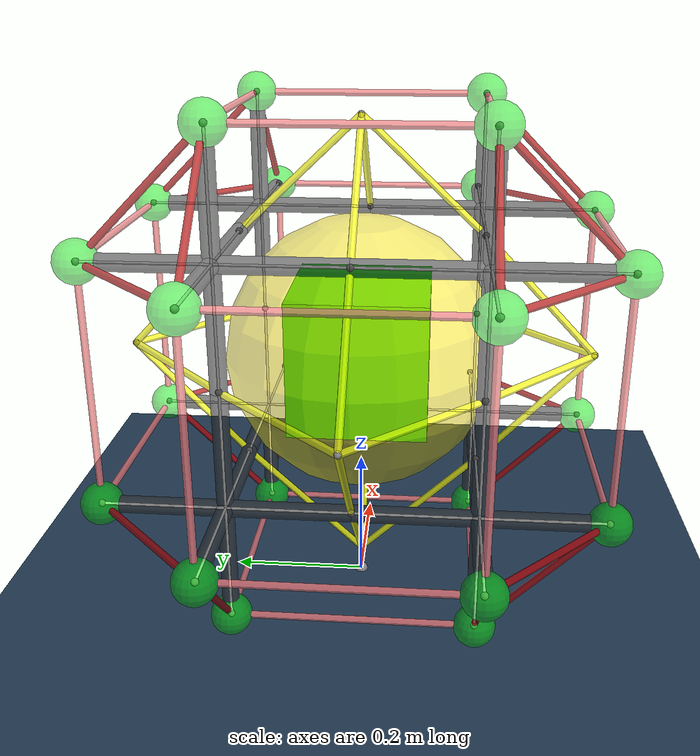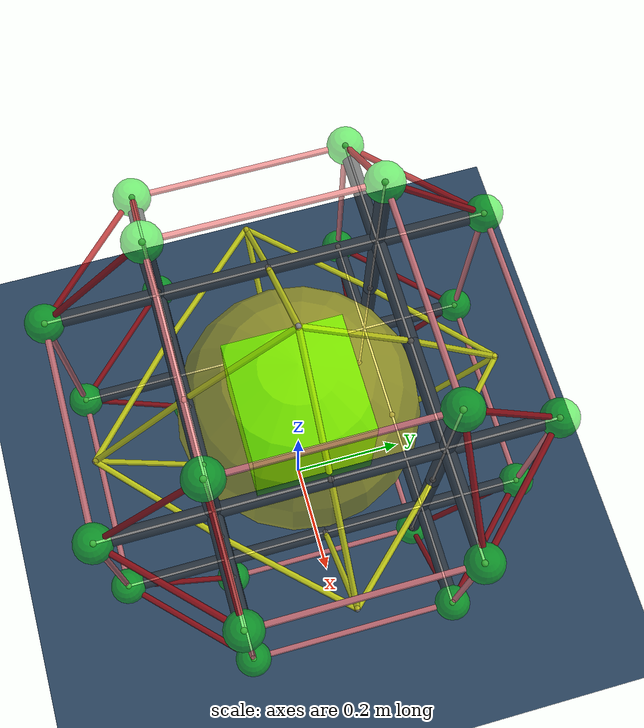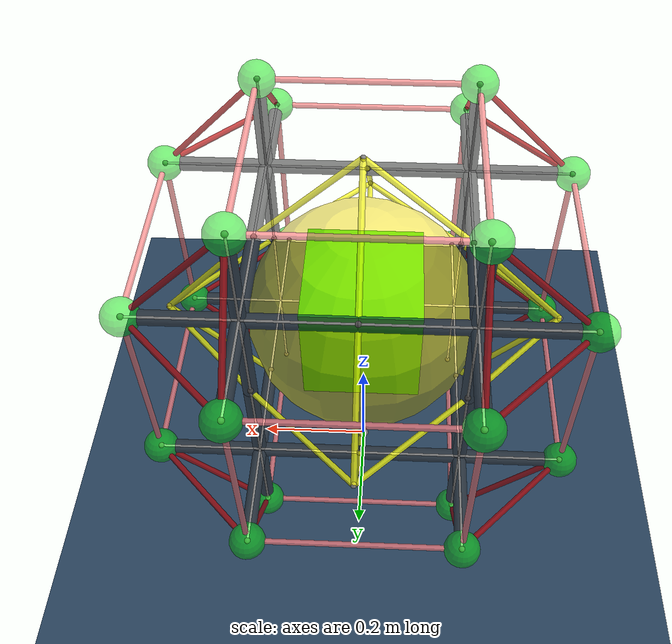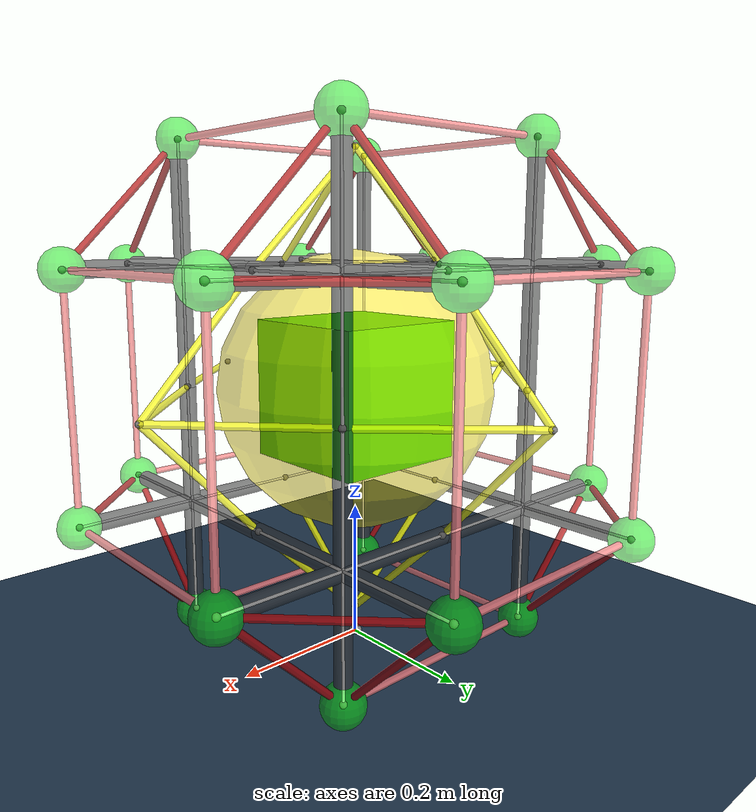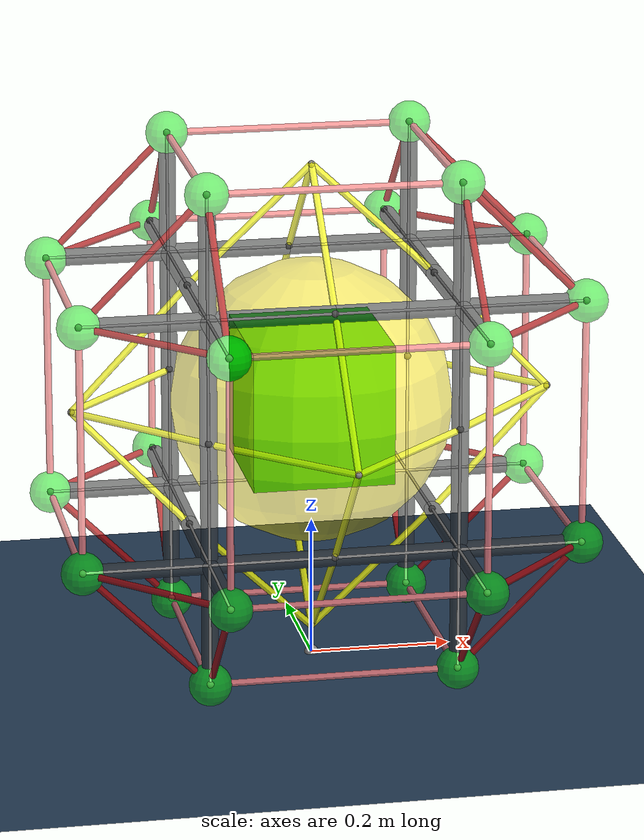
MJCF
<?xml version='1.0' encoding='utf-8'?>
<mujoco model="TT12_environment">
  <compiler autolimits="true" coordinate="local" angle="degree" inertiafromgeom="true" />
  <option timestep="1e-06" gravity="0 0 -10" integrator="Euler">
    <flag override="disable" energy="enable" />
  </option>
  <visual>
    <headlight ambient="0.59999999999999998 0.59999999999999998 0.59999999999999998" diffuse="0.29999999999999999 0.29999999999999999 0.29999999999999999" specular="0.10000000000000001 0.10000000000000001 0.10000000000000001" />
  </visual>
  <default>
    <default class="/">
      <joint type="hinge" damping="0" />
      <geom type="capsule" />
      <site type="sphere" size="0.01" />
      <tendon limited="true" range="0 10" width="0.0050000000000000001" rgba="1 0 0 1" damping="10" />
    </default>
    <default class="tt_model_0/">
      <tendon limited="true" range="0 10" width="0.0050000000000000001" rgba="1 0 0 1" damping="10" />
    </default>
    <default class="tt_model_0/rod0_1/" />
    <default class="tt_model_0/rod2_3/" />
    <default class="tt_model_0/rod4_5/" />
    <default class="tt_model_0/rod6_7/" />
    <default class="tt_model_0/rod8_9/" />
    <default class="tt_model_0/rod10_11/" />
    <default class="tt_model_0/rod12_13/" />
    <default class="tt_model_0/rod14_15/" />
    <default class="tt_model_0/rod16_17/" />
    <default class="tt_model_0/rod18_19/" />
    <default class="tt_model_0/rod20_21/" />
    <default class="tt_model_0/rod22_23/" />
    <default class="tt_model_0/middle_platform/" />
  </default>
  <asset>
    <texture name="skybox" type="skybox" builtin="gradient" rgb1="0.29999999999999999 0.5 0.69999999999999996" rgb2="0 0 0" width="512" height="3072" />
    <texture name="2d" type="2d" builtin="checker" rgb1="0.20000000000000001 0.29999999999999999 0.40000000000000002" rgb2="0.10000000000000001 0.20000000000000001 0.29999999999999999" width="300" height="300" />
    <material name="grid" class="/" texture="2d" texrepeat="5 5" reflectance="0.20000000000000001" />
  </asset>
  <worldbody>
    <geom name="floor" class="/" type="plane" condim="6" priority="1" size="0 0 0.125" material="grid" friction="0.5 0.53913327838919212 0.019243073269965646" solref="-4360.3889461536301 -138.02062726106232" solimp="0.96988191425750825 0.10222059345169457 0.055102813760108824 0.5 2" pos="0 0 0" />
    <light name="light_-2" class="/" pos="-2 -1 3" dir="2 1 -2" />
    <light name="light_2" class="/" pos="2 -1 3" dir="-2 1 -2" />
    <site name="world_site" class="/" pos="0 0 0" />
    <site name="tt_model_0/middle_site_0_1" class="tt_model_0/" rgba="0 0 0 0" pos="0.17499999999999999 0.17499999999999999 0.38" />
    <body pos="0.17499999999999999 0.17499999999999999 0.38" name="tt_model_0/rod0_1/">
      <freejoint name="tt_model_0/rod0_1/" />
      <geom name="tt_model_0/rod0_1/geom_from" class="tt_model_0/rod0_1/" type="cylinder" size="0.012" rgba="0.20000000000000001 0.20000000000000001 0.20000000000000001 0.59999999999999998" mass="0.01125" fromto="0 0 0.34999999999999998 0 0 0" />
      <body name="tt_model_0/rod0_1/body_to" pos="0 0 0">
        <geom name="tt_model_0/rod0_1/geom_to" class="tt_model_0/rod0_1/" type="cylinder" size="0.012" rgba="0.20000000000000001 0.20000000000000001 0.20000000000000001 0.59999999999999998" mass="0.01125" fromto="0 0 0 0 0 -0.34999999999999998" />
        <joint name="tt_model_0/rod0_1/slide_to" class="tt_model_0/rod0_1/" type="slide" axis="0 0 1" limited="true" range="-0.5 0.5" />
        <site name="tt_model_0/rod0_1/node_1" class="tt_model_0/rod0_1/" pos="0 0 -0.34999999999999998" />
        <geom name="tt_model_0/rod0_1/geom_edge_1" class="tt_model_0/rod0_1/" type="sphere" condim="6" size="0.029999999999999999" rgba="0 0.90000000000000002 0 0.5" mass="0.011299999999999999" pos="0 0 -0.34999999999999998" />
      </body>
      <site name="tt_model_0/rod0_1/node_0" class="tt_model_0/rod0_1/" pos="0 0 0.34999999999999998" />
      <site name="tt_model_0/rod0_1/node_24" class="tt_model_0/rod0_1/" pos="0 0 0" />
      <geom name="tt_model_0/rod0_1/geom_edge_0" class="tt_model_0/rod0_1/" type="sphere" condim="6" size="0.029999999999999999" rgba="0 0.90000000000000002 0 0.5" mass="0.011299999999999999" pos="0 0 0.34999999999999998" />
    </body>
    <site name="tt_model_0/middle_site_2_3" class="tt_model_0/" rgba="0 0 0 0" pos="-0.17499999999999999 0.17499999999999999 0.38" />
    <body pos="-0.17499999999999999 0.17499999999999999 0.38" name="tt_model_0/rod2_3/">
      <freejoint name="tt_model_0/rod2_3/" />
      <geom name="tt_model_0/rod2_3/geom_from" class="tt_model_0/rod2_3/" type="cylinder" size="0.012" rgba="0.20000000000000001 0.20000000000000001 0.20000000000000001 0.59999999999999998" mass="0.01125" fromto="0 0 0.34999999999999998 0 0 0" />
      <body name="tt_model_0/rod2_3/body_to" pos="0 0 0">
        <geom name="tt_model_0/rod2_3/geom_to" class="tt_model_0/rod2_3/" type="cylinder" size="0.012" rgba="0.20000000000000001 0.20000000000000001 0.20000000000000001 0.59999999999999998" mass="0.01125" fromto="0 0 0 0 0 -0.34999999999999998" />
        <joint name="tt_model_0/rod2_3/slide_to" class="tt_model_0/rod2_3/" type="slide" axis="0 0 1" limited="true" range="-0.5 0.5" />
        <site name="tt_model_0/rod2_3/node_3" class="tt_model_0/rod2_3/" pos="0 0 -0.34999999999999998" />
        <geom name="tt_model_0/rod2_3/geom_edge_3" class="tt_model_0/rod2_3/" type="sphere" condim="6" size="0.029999999999999999" rgba="0 0.90000000000000002 0 0.5" mass="0.011299999999999999" pos="0 0 -0.34999999999999998" />
      </body>
      <site name="tt_model_0/rod2_3/node_2" class="tt_model_0/rod2_3/" pos="0 0 0.34999999999999998" />
      <site name="tt_model_0/rod2_3/node_25" class="tt_model_0/rod2_3/" pos="0 0 0" />
      <geom name="tt_model_0/rod2_3/geom_edge_2" class="tt_model_0/rod2_3/" type="sphere" condim="6" size="0.029999999999999999" rgba="0 0.90000000000000002 0 0.5" mass="0.011299999999999999" pos="0 0 0.34999999999999998" />
    </body>
    <site name="tt_model_0/middle_site_4_5" class="tt_model_0/" rgba="0 0 0 0" pos="-0.17499999999999999 -0.17499999999999999 0.38" />
    <body pos="-0.17499999999999999 -0.17499999999999999 0.38" name="tt_model_0/rod4_5/">
      <freejoint name="tt_model_0/rod4_5/" />
      <geom name="tt_model_0/rod4_5/geom_from" class="tt_model_0/rod4_5/" type="cylinder" size="0.012" rgba="0.20000000000000001 0.20000000000000001 0.20000000000000001 0.59999999999999998" mass="0.01125" fromto="0 0 0.34999999999999998 0 0 0" />
      <body name="tt_model_0/rod4_5/body_to" pos="0 0 0">
        <geom name="tt_model_0/rod4_5/geom_to" class="tt_model_0/rod4_5/" type="cylinder" size="0.012" rgba="0.20000000000000001 0.20000000000000001 0.20000000000000001 0.59999999999999998" mass="0.01125" fromto="0 0 0 0 0 -0.34999999999999998" />
        <joint name="tt_model_0/rod4_5/slide_to" class="tt_model_0/rod4_5/" type="slide" axis="0 0 1" limited="true" range="-0.5 0.5" />
        <site name="tt_model_0/rod4_5/node_5" class="tt_model_0/rod4_5/" pos="0 0 -0.34999999999999998" />
        <geom name="tt_model_0/rod4_5/geom_edge_5" class="tt_model_0/rod4_5/" type="sphere" condim="6" size="0.029999999999999999" rgba="0 0.90000000000000002 0 0.5" mass="0.011299999999999999" pos="0 0 -0.34999999999999998" />
      </body>
      <site name="tt_model_0/rod4_5/node_4" class="tt_model_0/rod4_5/" pos="0 0 0.34999999999999998" />
      <site name="tt_model_0/rod4_5/node_26" class="tt_model_0/rod4_5/" pos="0 0 0" />
      <geom name="tt_model_0/rod4_5/geom_edge_4" class="tt_model_0/rod4_5/" type="sphere" condim="6" size="0.029999999999999999" rgba="0 0.90000000000000002 0 0.5" mass="0.011299999999999999" pos="0 0 0.34999999999999998" />
    </body>
    <site name="tt_model_0/middle_site_6_7" class="tt_model_0/" rgba="0 0 0 0" pos="0.17499999999999999 -0.17499999999999999 0.38" />
    <body pos="0.17499999999999999 -0.17499999999999999 0.38" name="tt_model_0/rod6_7/">
      <freejoint name="tt_model_0/rod6_7/" />
      <geom name="tt_model_0/rod6_7/geom_from" class="tt_model_0/rod6_7/" type="cylinder" size="0.012" rgba="0.20000000000000001 0.20000000000000001 0.20000000000000001 0.59999999999999998" mass="0.01125" fromto="0 0 0.34999999999999998 0 0 0" />
      <body name="tt_model_0/rod6_7/body_to" pos="0 0 0">
        <geom name="tt_model_0/rod6_7/geom_to" class="tt_model_0/rod6_7/" type="cylinder" size="0.012" rgba="0.20000000000000001 0.20000000000000001 0.20000000000000001 0.59999999999999998" mass="0.01125" fromto="0 0 0 0 0 -0.34999999999999998" />
        <joint name="tt_model_0/rod6_7/slide_to" class="tt_model_0/rod6_7/" type="slide" axis="0 0 1" limited="true" range="-0.5 0.5" />
        <site name="tt_model_0/rod6_7/node_7" class="tt_model_0/rod6_7/" pos="0 0 -0.34999999999999998" />
        <geom name="tt_model_0/rod6_7/geom_edge_7" class="tt_model_0/rod6_7/" type="sphere" condim="6" size="0.029999999999999999" rgba="0 0.90000000000000002 0 0.5" mass="0.011299999999999999" pos="0 0 -0.34999999999999998" />
      </body>
      <site name="tt_model_0/rod6_7/node_6" class="tt_model_0/rod6_7/" pos="0 0 0.34999999999999998" />
      <site name="tt_model_0/rod6_7/node_27" class="tt_model_0/rod6_7/" pos="0 0 0" />
      <geom name="tt_model_0/rod6_7/geom_edge_6" class="tt_model_0/rod6_7/" type="sphere" condim="6" size="0.029999999999999999" rgba="0 0.90000000000000002 0 0.5" mass="0.011299999999999999" pos="0 0 0.34999999999999998" />
    </body>
    <site name="tt_model_0/middle_site_8_9" class="tt_model_0/" rgba="0 0 0 0" pos="0.17499999999999999 0 0.55499999999999994" />
    <body pos="0.17499999999999999 0 0.55499999999999994" name="tt_model_0/rod8_9/">
      <freejoint name="tt_model_0/rod8_9/" />
      <geom name="tt_model_0/rod8_9/geom_from" class="tt_model_0/rod8_9/" type="cylinder" size="0.012" rgba="0.20000000000000001 0.20000000000000001 0.20000000000000001 0.59999999999999998" mass="0.01125" fromto="0 0.34999999999999998 0 0 0 0" />
      <body name="tt_model_0/rod8_9/body_to" pos="0 0 0">
        <geom name="tt_model_0/rod8_9/geom_to" class="tt_model_0/rod8_9/" type="cylinder" size="0.012" rgba="0.20000000000000001 0.20000000000000001 0.20000000000000001 0.59999999999999998" mass="0.01125" fromto="0 0 0 0 -0.34999999999999998 0" />
        <joint name="tt_model_0/rod8_9/slide_to" class="tt_model_0/rod8_9/" type="slide" axis="0 1 0" limited="true" range="-0.5 0.5" />
        <site name="tt_model_0/rod8_9/node_9" class="tt_model_0/rod8_9/" pos="0 -0.34999999999999998 0" />
        <geom name="tt_model_0/rod8_9/geom_edge_9" class="tt_model_0/rod8_9/" type="sphere" condim="6" size="0.029999999999999999" rgba="0 0.90000000000000002 0 0.5" mass="0.011299999999999999" pos="0 -0.34999999999999998 0" />
      </body>
      <site name="tt_model_0/rod8_9/node_8" class="tt_model_0/rod8_9/" pos="0 0.34999999999999998 0" />
      <site name="tt_model_0/rod8_9/node_28" class="tt_model_0/rod8_9/" pos="0 0 0" />
      <geom name="tt_model_0/rod8_9/geom_edge_8" class="tt_model_0/rod8_9/" type="sphere" condim="6" size="0.029999999999999999" rgba="0 0.90000000000000002 0 0.5" mass="0.011299999999999999" pos="0 0.34999999999999998 0" />
    </body>
    <site name="tt_model_0/middle_site_10_11" class="tt_model_0/" rgba="0 0 0 0" pos="0.17499999999999999 0 0.20500000000000002" />
    <body pos="0.17499999999999999 0 0.20500000000000002" name="tt_model_0/rod10_11/">
      <freejoint name="tt_model_0/rod10_11/" />
      <geom name="tt_model_0/rod10_11/geom_from" class="tt_model_0/rod10_11/" type="cylinder" size="0.012" rgba="0.20000000000000001 0.20000000000000001 0.20000000000000001 0.59999999999999998" mass="0.01125" fromto="0 0.34999999999999998 0 0 0 0" />
      <body name="tt_model_0/rod10_11/body_to" pos="0 0 0">
        <geom name="tt_model_0/rod10_11/geom_to" class="tt_model_0/rod10_11/" type="cylinder" size="0.012" rgba="0.20000000000000001 0.20000000000000001 0.20000000000000001 0.59999999999999998" mass="0.01125" fromto="0 0 0 0 -0.34999999999999998 0" />
        <joint name="tt_model_0/rod10_11/slide_to" class="tt_model_0/rod10_11/" type="slide" axis="0 1 0" limited="true" range="-0.5 0.5" />
        <site name="tt_model_0/rod10_11/node_11" class="tt_model_0/rod10_11/" pos="0 -0.34999999999999998 0" />
        <geom name="tt_model_0/rod10_11/geom_edge_11" class="tt_model_0/rod10_11/" type="sphere" condim="6" size="0.029999999999999999" rgba="0 0.90000000000000002 0 0.5" mass="0.011299999999999999" pos="0 -0.34999999999999998 0" />
      </body>
      <site name="tt_model_0/rod10_11/node_10" class="tt_model_0/rod10_11/" pos="0 0.34999999999999998 0" />
      <site name="tt_model_0/rod10_11/node_29" class="tt_model_0/rod10_11/" pos="0 0 0" />
      <geom name="tt_model_0/rod10_11/geom_edge_10" class="tt_model_0/rod10_11/" type="sphere" condim="6" size="0.029999999999999999" rgba="0 0.90000000000000002 0 0.5" mass="0.011299999999999999" pos="0 0.34999999999999998 0" />
    </body>
    <site name="tt_model_0/middle_site_12_13" class="tt_model_0/" rgba="0 0 0 0" pos="-0.17499999999999999 0 0.20500000000000002" />
    <body pos="-0.17499999999999999 0 0.20500000000000002" name="tt_model_0/rod12_13/">
      <freejoint name="tt_model_0/rod12_13/" />
      <geom name="tt_model_0/rod12_13/geom_from" class="tt_model_0/rod12_13/" type="cylinder" size="0.012" rgba="0.20000000000000001 0.20000000000000001 0.20000000000000001 0.59999999999999998" mass="0.01125" fromto="0 0.34999999999999998 0 0 0 0" />
      <body name="tt_model_0/rod12_13/body_to" pos="0 0 0">
        <geom name="tt_model_0/rod12_13/geom_to" class="tt_model_0/rod12_13/" type="cylinder" size="0.012" rgba="0.20000000000000001 0.20000000000000001 0.20000000000000001 0.59999999999999998" mass="0.01125" fromto="0 0 0 0 -0.34999999999999998 0" />
        <joint name="tt_model_0/rod12_13/slide_to" class="tt_model_0/rod12_13/" type="slide" axis="0 1 0" limited="true" range="-0.5 0.5" />
        <site name="tt_model_0/rod12_13/node_13" class="tt_model_0/rod12_13/" pos="0 -0.34999999999999998 0" />
        <geom name="tt_model_0/rod12_13/geom_edge_13" class="tt_model_0/rod12_13/" type="sphere" condim="6" size="0.029999999999999999" rgba="0 0.90000000000000002 0 0.5" mass="0.011299999999999999" pos="0 -0.34999999999999998 0" />
      </body>
      <site name="tt_model_0/rod12_13/node_12" class="tt_model_0/rod12_13/" pos="0 0.34999999999999998 0" />
      <site name="tt_model_0/rod12_13/node_30" class="tt_model_0/rod12_13/" pos="0 0 0" />
      <geom name="tt_model_0/rod12_13/geom_edge_12" class="tt_model_0/rod12_13/" type="sphere" condim="6" size="0.029999999999999999" rgba="0 0.90000000000000002 0 0.5" mass="0.011299999999999999" pos="0 0.34999999999999998 0" />
    </body>
    <site name="tt_model_0/middle_site_14_15" class="tt_model_0/" rgba="0 0 0 0" pos="-0.17499999999999999 0 0.55499999999999994" />
    <body pos="-0.17499999999999999 0 0.55499999999999994" name="tt_model_0/rod14_15/">
      <freejoint name="tt_model_0/rod14_15/" />
      <geom name="tt_model_0/rod14_15/geom_from" class="tt_model_0/rod14_15/" type="cylinder" size="0.012" rgba="0.20000000000000001 0.20000000000000001 0.20000000000000001 0.59999999999999998" mass="0.01125" fromto="0 0.34999999999999998 0 0 0 0" />
      <body name="tt_model_0/rod14_15/body_to" pos="0 0 0">
        <geom name="tt_model_0/rod14_15/geom_to" class="tt_model_0/rod14_15/" type="cylinder" size="0.012" rgba="0.20000000000000001 0.20000000000000001 0.20000000000000001 0.59999999999999998" mass="0.01125" fromto="0 0 0 0 -0.34999999999999998 0" />
        <joint name="tt_model_0/rod14_15/slide_to" class="tt_model_0/rod14_15/" type="slide" axis="0 1 0" limited="true" range="-0.5 0.5" />
        <site name="tt_model_0/rod14_15/node_15" class="tt_model_0/rod14_15/" pos="0 -0.34999999999999998 0" />
        <geom name="tt_model_0/rod14_15/geom_edge_15" class="tt_model_0/rod14_15/" type="sphere" condim="6" size="0.029999999999999999" rgba="0 0.90000000000000002 0 0.5" mass="0.011299999999999999" pos="0 -0.34999999999999998 0" />
      </body>
      <site name="tt_model_0/rod14_15/node_14" class="tt_model_0/rod14_15/" pos="0 0.34999999999999998 0" />
      <site name="tt_model_0/rod14_15/node_31" class="tt_model_0/rod14_15/" pos="0 0 0" />
      <geom name="tt_model_0/rod14_15/geom_edge_14" class="tt_model_0/rod14_15/" type="sphere" condim="6" size="0.029999999999999999" rgba="0 0.90000000000000002 0 0.5" mass="0.011299999999999999" pos="0 0.34999999999999998 0" />
    </body>
    <site name="tt_model_0/middle_site_16_17" class="tt_model_0/" rgba="0 0 0 0" pos="0 0.17499999999999999 0.55499999999999994" />
    <body pos="0 0.17499999999999999 0.55499999999999994" name="tt_model_0/rod16_17/">
      <freejoint name="tt_model_0/rod16_17/" />
      <geom name="tt_model_0/rod16_17/geom_from" class="tt_model_0/rod16_17/" type="cylinder" size="0.012" rgba="0.20000000000000001 0.20000000000000001 0.20000000000000001 0.59999999999999998" mass="0.01125" fromto="0.34999999999999998 0 0 0 0 0" />
      <body name="tt_model_0/rod16_17/body_to" pos="0 0 0">
        <geom name="tt_model_0/rod16_17/geom_to" class="tt_model_0/rod16_17/" type="cylinder" size="0.012" rgba="0.20000000000000001 0.20000000000000001 0.20000000000000001 0.59999999999999998" mass="0.01125" fromto="0 0 0 -0.34999999999999998 0 0" />
        <joint name="tt_model_0/rod16_17/slide_to" class="tt_model_0/rod16_17/" type="slide" axis="1 0 0" limited="true" range="-0.5 0.5" />
        <site name="tt_model_0/rod16_17/node_17" class="tt_model_0/rod16_17/" pos="-0.34999999999999998 0 0" />
        <geom name="tt_model_0/rod16_17/geom_edge_17" class="tt_model_0/rod16_17/" type="sphere" condim="6" size="0.029999999999999999" rgba="0 0.90000000000000002 0 0.5" mass="0.011299999999999999" pos="-0.34999999999999998 0 0" />
      </body>
      <site name="tt_model_0/rod16_17/node_16" class="tt_model_0/rod16_17/" pos="0.34999999999999998 0 0" />
      <site name="tt_model_0/rod16_17/node_32" class="tt_model_0/rod16_17/" pos="0 0 0" />
      <geom name="tt_model_0/rod16_17/geom_edge_16" class="tt_model_0/rod16_17/" type="sphere" condim="6" size="0.029999999999999999" rgba="0 0.90000000000000002 0 0.5" mass="0.011299999999999999" pos="0.34999999999999998 0 0" />
    </body>
    <site name="tt_model_0/middle_site_18_19" class="tt_model_0/" rgba="0 0 0 0" pos="0 -0.17499999999999999 0.55499999999999994" />
    <body pos="0 -0.17499999999999999 0.55499999999999994" name="tt_model_0/rod18_19/">
      <freejoint name="tt_model_0/rod18_19/" />
      <geom name="tt_model_0/rod18_19/geom_from" class="tt_model_0/rod18_19/" type="cylinder" size="0.012" rgba="0.20000000000000001 0.20000000000000001 0.20000000000000001 0.59999999999999998" mass="0.01125" fromto="0.34999999999999998 0 0 0 0 0" />
      <body name="tt_model_0/rod18_19/body_to" pos="0 0 0">
        <geom name="tt_model_0/rod18_19/geom_to" class="tt_model_0/rod18_19/" type="cylinder" size="0.012" rgba="0.20000000000000001 0.20000000000000001 0.20000000000000001 0.59999999999999998" mass="0.01125" fromto="0 0 0 -0.34999999999999998 0 0" />
        <joint name="tt_model_0/rod18_19/slide_to" class="tt_model_0/rod18_19/" type="slide" axis="1 0 0" limited="true" range="-0.5 0.5" />
        <site name="tt_model_0/rod18_19/node_19" class="tt_model_0/rod18_19/" pos="-0.34999999999999998 0 0" />
        <geom name="tt_model_0/rod18_19/geom_edge_19" class="tt_model_0/rod18_19/" type="sphere" condim="6" size="0.029999999999999999" rgba="0 0.90000000000000002 0 0.5" mass="0.011299999999999999" pos="-0.34999999999999998 0 0" />
      </body>
      <site name="tt_model_0/rod18_19/node_18" class="tt_model_0/rod18_19/" pos="0.34999999999999998 0 0" />
      <site name="tt_model_0/rod18_19/node_33" class="tt_model_0/rod18_19/" pos="0 0 0" />
      <geom name="tt_model_0/rod18_19/geom_edge_18" class="tt_model_0/rod18_19/" type="sphere" condim="6" size="0.029999999999999999" rgba="0 0.90000000000000002 0 0.5" mass="0.011299999999999999" pos="0.34999999999999998 0 0" />
    </body>
    <site name="tt_model_0/middle_site_20_21" class="tt_model_0/" rgba="0 0 0 0" pos="0 -0.17499999999999999 0.20500000000000002" />
    <body pos="0 -0.17499999999999999 0.20500000000000002" name="tt_model_0/rod20_21/">
      <freejoint name="tt_model_0/rod20_21/" />
      <geom name="tt_model_0/rod20_21/geom_from" class="tt_model_0/rod20_21/" type="cylinder" size="0.012" rgba="0.20000000000000001 0.20000000000000001 0.20000000000000001 0.59999999999999998" mass="0.01125" fromto="0.34999999999999998 0 0 0 0 0" />
      <body name="tt_model_0/rod20_21/body_to" pos="0 0 0">
        <geom name="tt_model_0/rod20_21/geom_to" class="tt_model_0/rod20_21/" type="cylinder" size="0.012" rgba="0.20000000000000001 0.20000000000000001 0.20000000000000001 0.59999999999999998" mass="0.01125" fromto="0 0 0 -0.34999999999999998 0 0" />
        <joint name="tt_model_0/rod20_21/slide_to" class="tt_model_0/rod20_21/" type="slide" axis="1 0 0" limited="true" range="-0.5 0.5" />
        <site name="tt_model_0/rod20_21/node_21" class="tt_model_0/rod20_21/" pos="-0.34999999999999998 0 0" />
        <geom name="tt_model_0/rod20_21/geom_edge_21" class="tt_model_0/rod20_21/" type="sphere" condim="6" size="0.029999999999999999" rgba="0 0.90000000000000002 0 0.5" mass="0.011299999999999999" pos="-0.34999999999999998 0 0" />
      </body>
      <site name="tt_model_0/rod20_21/node_20" class="tt_model_0/rod20_21/" pos="0.34999999999999998 0 0" />
      <site name="tt_model_0/rod20_21/node_34" class="tt_model_0/rod20_21/" pos="0 0 0" />
      <geom name="tt_model_0/rod20_21/geom_edge_20" class="tt_model_0/rod20_21/" type="sphere" condim="6" size="0.029999999999999999" rgba="0 0.90000000000000002 0 0.5" mass="0.011299999999999999" pos="0.34999999999999998 0 0" />
    </body>
    <site name="tt_model_0/middle_site_22_23" class="tt_model_0/" rgba="0 0 0 0" pos="0 0.17499999999999999 0.20500000000000002" />
    <body pos="0 0.17499999999999999 0.20500000000000002" name="tt_model_0/rod22_23/">
      <freejoint name="tt_model_0/rod22_23/" />
      <geom name="tt_model_0/rod22_23/geom_from" class="tt_model_0/rod22_23/" type="cylinder" size="0.012" rgba="0.20000000000000001 0.20000000000000001 0.20000000000000001 0.59999999999999998" mass="0.01125" fromto="0.34999999999999998 0 0 0 0 0" />
      <body name="tt_model_0/rod22_23/body_to" pos="0 0 0">
        <geom name="tt_model_0/rod22_23/geom_to" class="tt_model_0/rod22_23/" type="cylinder" size="0.012" rgba="0.20000000000000001 0.20000000000000001 0.20000000000000001 0.59999999999999998" mass="0.01125" fromto="0 0 0 -0.34999999999999998 0 0" />
        <joint name="tt_model_0/rod22_23/slide_to" class="tt_model_0/rod22_23/" type="slide" axis="1 0 0" limited="true" range="-0.5 0.5" />
        <site name="tt_model_0/rod22_23/node_23" class="tt_model_0/rod22_23/" pos="-0.34999999999999998 0 0" />
        <geom name="tt_model_0/rod22_23/geom_edge_23" class="tt_model_0/rod22_23/" type="sphere" condim="6" size="0.029999999999999999" rgba="0 0.90000000000000002 0 0.5" mass="0.011299999999999999" pos="-0.34999999999999998 0 0" />
      </body>
      <site name="tt_model_0/rod22_23/node_22" class="tt_model_0/rod22_23/" pos="0.34999999999999998 0 0" />
      <site name="tt_model_0/rod22_23/node_35" class="tt_model_0/rod22_23/" pos="0 0 0" />
      <geom name="tt_model_0/rod22_23/geom_edge_22" class="tt_model_0/rod22_23/" type="sphere" condim="6" size="0.029999999999999999" rgba="0 0.90000000000000002 0 0.5" mass="0.011299999999999999" pos="0.34999999999999998 0 0" />
    </body>
    <site name="tt_model_0/middle_element_site" class="tt_model_0/" rgba="0 0 0 0" pos="0 0 0.38" />
    <body pos="0 0 0.38" name="tt_model_0/middle_platform/">
      <freejoint name="tt_model_0/middle_platform/" />
      <inertial pos="0 0 0" mass="0.69999999999999996" diaginertia="0.02 0.02 0.02" />
      <site name="tt_model_0/middle_platform/node_38" class="tt_model_0/middle_platform/" pos="-0.34000000000000002 0 0" />
      <site name="tt_model_0/middle_platform/node_39" class="tt_model_0/middle_platform/" pos="0 0.34000000000000002 0" />
      <site name="tt_model_0/middle_platform/node_40" class="tt_model_0/middle_platform/" pos="0 -0.34000000000000002 0" />
      <site name="tt_model_0/middle_platform/node_41" class="tt_model_0/middle_platform/" pos="0 0 0.33999999999999997" />
      <site name="tt_model_0/middle_platform/node_42" class="tt_model_0/middle_platform/" pos="0 0 -0.34000000000000002" />
      <site name="tt_model_0/middle_platform/node_37" class="tt_model_0/middle_platform/" pos="0.34000000000000002 0 0" />
      <site name="tt_model_0/middle_platform/outside_site" class="tt_model_0/middle_platform/" rgba="1 0.90000000000000002 0 0.5" size="0.20000000000000001" pos="0 0 0" />
      <body name="tt_model_0/middle_platform/inside_ball" pos="0 0 0">
        <inertial pos="0 0 0" mass="6.5999999999999996" diaginertia="0.12 0.12 0.12" />
        <joint name="tt_model_0/middle_platform/x_control" class="tt_model_0/middle_platform/" type="hinge" axis="1 0 0" />
        <joint name="tt_model_0/middle_platform/y_control" class="tt_model_0/middle_platform/" type="hinge" axis="0 1 0" />
        <joint name="tt_model_0/middle_platform/z_control" class="tt_model_0/middle_platform/" type="hinge" axis="0 0 1" />
        <site name="tt_model_0/middle_platform/inside_site" class="tt_model_0/middle_platform/" type="box" rgba="0 0.90000000000000002 0 1" size="0.10000000000000001 0.10000000000000001 0.10000000000000001" pos="0 0 0" />
      </body>
    </body>
  </worldbody>
  <contact>
    <exclude name="tt_model_0/exclude_rod0_1_rod2_3" body1="tt_model_0/rod0_1/" body2="tt_model_0/rod2_3/" />
    <exclude name="tt_model_0/exclude_rod0_1_rod4_5" body1="tt_model_0/rod0_1/" body2="tt_model_0/rod4_5/" />
    <exclude name="tt_model_0/exclude_rod0_1_rod6_7" body1="tt_model_0/rod0_1/" body2="tt_model_0/rod6_7/" />
    <exclude name="tt_model_0/exclude_rod0_1_rod8_9" body1="tt_model_0/rod0_1/" body2="tt_model_0/rod8_9/" />
    <exclude name="tt_model_0/exclude_rod0_1_rod10_11" body1="tt_model_0/rod0_1/" body2="tt_model_0/rod10_11/" />
    <exclude name="tt_model_0/exclude_rod0_1_rod12_13" body1="tt_model_0/rod0_1/" body2="tt_model_0/rod12_13/" />
    <exclude name="tt_model_0/exclude_rod0_1_rod14_15" body1="tt_model_0/rod0_1/" body2="tt_model_0/rod14_15/" />
    <exclude name="tt_model_0/exclude_rod0_1_rod16_17" body1="tt_model_0/rod0_1/" body2="tt_model_0/rod16_17/" />
    <exclude name="tt_model_0/exclude_rod0_1_rod18_19" body1="tt_model_0/rod0_1/" body2="tt_model_0/rod18_19/" />
    <exclude name="tt_model_0/exclude_rod0_1_rod20_21" body1="tt_model_0/rod0_1/" body2="tt_model_0/rod20_21/" />
    <exclude name="tt_model_0/exclude_rod0_1_rod22_23" body1="tt_model_0/rod0_1/" body2="tt_model_0/rod22_23/" />
    <exclude name="tt_model_0/exclude_rod2_3_rod4_5" body1="tt_model_0/rod2_3/" body2="tt_model_0/rod4_5/" />
    <exclude name="tt_model_0/exclude_rod2_3_rod6_7" body1="tt_model_0/rod2_3/" body2="tt_model_0/rod6_7/" />
    <exclude name="tt_model_0/exclude_rod2_3_rod8_9" body1="tt_model_0/rod2_3/" body2="tt_model_0/rod8_9/" />
    <exclude name="tt_model_0/exclude_rod2_3_rod10_11" body1="tt_model_0/rod2_3/" body2="tt_model_0/rod10_11/" />
    <exclude name="tt_model_0/exclude_rod2_3_rod12_13" body1="tt_model_0/rod2_3/" body2="tt_model_0/rod12_13/" />
    <exclude name="tt_model_0/exclude_rod2_3_rod14_15" body1="tt_model_0/rod2_3/" body2="tt_model_0/rod14_15/" />
    <exclude name="tt_model_0/exclude_rod2_3_rod16_17" body1="tt_model_0/rod2_3/" body2="tt_model_0/rod16_17/" />
    <exclude name="tt_model_0/exclude_rod2_3_rod18_19" body1="tt_model_0/rod2_3/" body2="tt_model_0/rod18_19/" />
    <exclude name="tt_model_0/exclude_rod2_3_rod20_21" body1="tt_model_0/rod2_3/" body2="tt_model_0/rod20_21/" />
    <exclude name="tt_model_0/exclude_rod2_3_rod22_23" body1="tt_model_0/rod2_3/" body2="tt_model_0/rod22_23/" />
    <exclude name="tt_model_0/exclude_rod4_5_rod6_7" body1="tt_model_0/rod4_5/" body2="tt_model_0/rod6_7/" />
    <exclude name="tt_model_0/exclude_rod4_5_rod8_9" body1="tt_model_0/rod4_5/" body2="tt_model_0/rod8_9/" />
    <exclude name="tt_model_0/exclude_rod4_5_rod10_11" body1="tt_model_0/rod4_5/" body2="tt_model_0/rod10_11/" />
    <exclude name="tt_model_0/exclude_rod4_5_rod12_13" body1="tt_model_0/rod4_5/" body2="tt_model_0/rod12_13/" />
    <exclude name="tt_model_0/exclude_rod4_5_rod14_15" body1="tt_model_0/rod4_5/" body2="tt_model_0/rod14_15/" />
    <exclude name="tt_model_0/exclude_rod4_5_rod16_17" body1="tt_model_0/rod4_5/" body2="tt_model_0/rod16_17/" />
    <exclude name="tt_model_0/exclude_rod4_5_rod18_19" body1="tt_model_0/rod4_5/" body2="tt_model_0/rod18_19/" />
    <exclude name="tt_model_0/exclude_rod4_5_rod20_21" body1="tt_model_0/rod4_5/" body2="tt_model_0/rod20_21/" />
    <exclude name="tt_model_0/exclude_rod4_5_rod22_23" body1="tt_model_0/rod4_5/" body2="tt_model_0/rod22_23/" />
    <exclude name="tt_model_0/exclude_rod6_7_rod8_9" body1="tt_model_0/rod6_7/" body2="tt_model_0/rod8_9/" />
    <exclude name="tt_model_0/exclude_rod6_7_rod10_11" body1="tt_model_0/rod6_7/" body2="tt_model_0/rod10_11/" />
    <exclude name="tt_model_0/exclude_rod6_7_rod12_13" body1="tt_model_0/rod6_7/" body2="tt_model_0/rod12_13/" />
    <exclude name="tt_model_0/exclude_rod6_7_rod14_15" body1="tt_model_0/rod6_7/" body2="tt_model_0/rod14_15/" />
    <exclude name="tt_model_0/exclude_rod6_7_rod16_17" body1="tt_model_0/rod6_7/" body2="tt_model_0/rod16_17/" />
    <exclude name="tt_model_0/exclude_rod6_7_rod18_19" body1="tt_model_0/rod6_7/" body2="tt_model_0/rod18_19/" />
    <exclude name="tt_model_0/exclude_rod6_7_rod20_21" body1="tt_model_0/rod6_7/" body2="tt_model_0/rod20_21/" />
    <exclude name="tt_model_0/exclude_rod6_7_rod22_23" body1="tt_model_0/rod6_7/" body2="tt_model_0/rod22_23/" />
    <exclude name="tt_model_0/exclude_rod8_9_rod10_11" body1="tt_model_0/rod8_9/" body2="tt_model_0/rod10_11/" />
    <exclude name="tt_model_0/exclude_rod8_9_rod12_13" body1="tt_model_0/rod8_9/" body2="tt_model_0/rod12_13/" />
    <exclude name="tt_model_0/exclude_rod8_9_rod14_15" body1="tt_model_0/rod8_9/" body2="tt_model_0/rod14_15/" />
    <exclude name="tt_model_0/exclude_rod8_9_rod16_17" body1="tt_model_0/rod8_9/" body2="tt_model_0/rod16_17/" />
    <exclude name="tt_model_0/exclude_rod8_9_rod18_19" body1="tt_model_0/rod8_9/" body2="tt_model_0/rod18_19/" />
    <exclude name="tt_model_0/exclude_rod8_9_rod20_21" body1="tt_model_0/rod8_9/" body2="tt_model_0/rod20_21/" />
    <exclude name="tt_model_0/exclude_rod8_9_rod22_23" body1="tt_model_0/rod8_9/" body2="tt_model_0/rod22_23/" />
    <exclude name="tt_model_0/exclude_rod10_11_rod12_13" body1="tt_model_0/rod10_11/" body2="tt_model_0/rod12_13/" />
    <exclude name="tt_model_0/exclude_rod10_11_rod14_15" body1="tt_model_0/rod10_11/" body2="tt_model_0/rod14_15/" />
    <exclude name="tt_model_0/exclude_rod10_11_rod16_17" body1="tt_model_0/rod10_11/" body2="tt_model_0/rod16_17/" />
    <exclude name="tt_model_0/exclude_rod10_11_rod18_19" body1="tt_model_0/rod10_11/" body2="tt_model_0/rod18_19/" />
    <exclude name="tt_model_0/exclude_rod10_11_rod20_21" body1="tt_model_0/rod10_11/" body2="tt_model_0/rod20_21/" />
    <exclude name="tt_model_0/exclude_rod10_11_rod22_23" body1="tt_model_0/rod10_11/" body2="tt_model_0/rod22_23/" />
    <exclude name="tt_model_0/exclude_rod12_13_rod14_15" body1="tt_model_0/rod12_13/" body2="tt_model_0/rod14_15/" />
    <exclude name="tt_model_0/exclude_rod12_13_rod16_17" body1="tt_model_0/rod12_13/" body2="tt_model_0/rod16_17/" />
    <exclude name="tt_model_0/exclude_rod12_13_rod18_19" body1="tt_model_0/rod12_13/" body2="tt_model_0/rod18_19/" />
    <exclude name="tt_model_0/exclude_rod12_13_rod20_21" body1="tt_model_0/rod12_13/" body2="tt_model_0/rod20_21/" />
    <exclude name="tt_model_0/exclude_rod12_13_rod22_23" body1="tt_model_0/rod12_13/" body2="tt_model_0/rod22_23/" />
    <exclude name="tt_model_0/exclude_rod14_15_rod16_17" body1="tt_model_0/rod14_15/" body2="tt_model_0/rod16_17/" />
    <exclude name="tt_model_0/exclude_rod14_15_rod18_19" body1="tt_model_0/rod14_15/" body2="tt_model_0/rod18_19/" />
    <exclude name="tt_model_0/exclude_rod14_15_rod20_21" body1="tt_model_0/rod14_15/" body2="tt_model_0/rod20_21/" />
    <exclude name="tt_model_0/exclude_rod14_15_rod22_23" body1="tt_model_0/rod14_15/" body2="tt_model_0/rod22_23/" />
    <exclude name="tt_model_0/exclude_rod16_17_rod18_19" body1="tt_model_0/rod16_17/" body2="tt_model_0/rod18_19/" />
    <exclude name="tt_model_0/exclude_rod16_17_rod20_21" body1="tt_model_0/rod16_17/" body2="tt_model_0/rod20_21/" />
    <exclude name="tt_model_0/exclude_rod16_17_rod22_23" body1="tt_model_0/rod16_17/" body2="tt_model_0/rod22_23/" />
    <exclude name="tt_model_0/exclude_rod18_19_rod20_21" body1="tt_model_0/rod18_19/" body2="tt_model_0/rod20_21/" />
    <exclude name="tt_model_0/exclude_rod18_19_rod22_23" body1="tt_model_0/rod18_19/" body2="tt_model_0/rod22_23/" />
    <exclude name="tt_model_0/exclude_rod20_21_rod22_23" body1="tt_model_0/rod20_21/" body2="tt_model_0/rod22_23/" />
  </contact>
  <tendon>
    <spatial name="tt_model_0/spatial_bar_string_0_1" class="tt_model_0/" width="0.002" rgba="1 1 1 1" springlength="1.1101219330881975" stiffness="1000" damping="100">
      <site site="tt_model_0/rod0_1/node_0" />
      <site site="tt_model_0/rod0_1/node_1" />
    </spatial>
    <spatial name="tt_model_0/spatial_bar_string_2_3" class="tt_model_0/" width="0.002" rgba="1 1 1 1" springlength="1.1101219330881975" stiffness="1000" damping="100">
      <site site="tt_model_0/rod2_3/node_2" />
      <site site="tt_model_0/rod2_3/node_3" />
    </spatial>
    <spatial name="tt_model_0/spatial_bar_string_4_5" class="tt_model_0/" width="0.002" rgba="1 1 1 1" springlength="1.1101219330881975" stiffness="1000" damping="100">
      <site site="tt_model_0/rod4_5/node_4" />
      <site site="tt_model_0/rod4_5/node_5" />
    </spatial>
    <spatial name="tt_model_0/spatial_bar_string_6_7" class="tt_model_0/" width="0.002" rgba="1 1 1 1" springlength="1.1101219330881975" stiffness="1000" damping="100">
      <site site="tt_model_0/rod6_7/node_6" />
      <site site="tt_model_0/rod6_7/node_7" />
    </spatial>
    <spatial name="tt_model_0/spatial_bar_string_8_9" class="tt_model_0/" width="0.002" rgba="1 1 1 1" springlength="1.1101219330881975" stiffness="1000" damping="100">
      <site site="tt_model_0/rod8_9/node_8" />
      <site site="tt_model_0/rod8_9/node_9" />
    </spatial>
    <spatial name="tt_model_0/spatial_bar_string_10_11" class="tt_model_0/" width="0.002" rgba="1 1 1 1" springlength="1.1101219330881975" stiffness="1000" damping="100">
      <site site="tt_model_0/rod10_11/node_10" />
      <site site="tt_model_0/rod10_11/node_11" />
    </spatial>
    <spatial name="tt_model_0/spatial_bar_string_12_13" class="tt_model_0/" width="0.002" rgba="1 1 1 1" springlength="1.1101219330881975" stiffness="1000" damping="100">
      <site site="tt_model_0/rod12_13/node_12" />
      <site site="tt_model_0/rod12_13/node_13" />
    </spatial>
    <spatial name="tt_model_0/spatial_bar_string_14_15" class="tt_model_0/" width="0.002" rgba="1 1 1 1" springlength="1.1101219330881975" stiffness="1000" damping="100">
      <site site="tt_model_0/rod14_15/node_14" />
      <site site="tt_model_0/rod14_15/node_15" />
    </spatial>
    <spatial name="tt_model_0/spatial_bar_string_16_17" class="tt_model_0/" width="0.002" rgba="1 1 1 1" springlength="1.1101219330881975" stiffness="1000" damping="100">
      <site site="tt_model_0/rod16_17/node_16" />
      <site site="tt_model_0/rod16_17/node_17" />
    </spatial>
    <spatial name="tt_model_0/spatial_bar_string_18_19" class="tt_model_0/" width="0.002" rgba="1 1 1 1" springlength="1.1101219330881975" stiffness="1000" damping="100">
      <site site="tt_model_0/rod18_19/node_18" />
      <site site="tt_model_0/rod18_19/node_19" />
    </spatial>
    <spatial name="tt_model_0/spatial_bar_string_20_21" class="tt_model_0/" width="0.002" rgba="1 1 1 1" springlength="1.1101219330881975" stiffness="1000" damping="100">
      <site site="tt_model_0/rod20_21/node_20" />
      <site site="tt_model_0/rod20_21/node_21" />
    </spatial>
    <spatial name="tt_model_0/spatial_bar_string_22_23" class="tt_model_0/" width="0.002" rgba="1 1 1 1" springlength="1.1101219330881975" stiffness="1000" damping="100">
      <site site="tt_model_0/rod22_23/node_22" />
      <site site="tt_model_0/rod22_23/node_23" />
    </spatial>
    <spatial name="tt_model_0/td0_2" class="tt_model_0/" rgba="1 0.5 0.5 0.69999999999999996" springlength="0.22029831387808038" stiffness="771">
      <site site="tt_model_0/rod0_1/node_0" />
      <site site="tt_model_0/rod2_3/node_2" />
    </spatial>
    <spatial name="tt_model_0/td2_4" class="tt_model_0/" rgba="1 0.5 0.5 0.69999999999999996" springlength="0.22029831387808038" stiffness="771">
      <site site="tt_model_0/rod2_3/node_2" />
      <site site="tt_model_0/rod4_5/node_4" />
    </spatial>
    <spatial name="tt_model_0/td4_6" class="tt_model_0/" rgba="1 0.5 0.5 0.69999999999999996" springlength="0.22029831387808038" stiffness="771">
      <site site="tt_model_0/rod4_5/node_4" />
      <site site="tt_model_0/rod6_7/node_6" />
    </spatial>
    <spatial name="tt_model_0/td6_0" class="tt_model_0/" rgba="1 0.5 0.5 0.69999999999999996" springlength="0.22029831387808038" stiffness="771">
      <site site="tt_model_0/rod6_7/node_6" />
      <site site="tt_model_0/rod0_1/node_0" />
    </spatial>
    <spatial name="tt_model_0/td1_3" class="tt_model_0/" rgba="1 0.5 0.5 0.69999999999999996" springlength="0.22029831387808038" stiffness="771">
      <site site="tt_model_0/rod0_1/node_1" />
      <site site="tt_model_0/rod2_3/node_3" />
    </spatial>
    <spatial name="tt_model_0/td3_5" class="tt_model_0/" rgba="1 0.5 0.5 0.69999999999999996" springlength="0.22029831387808038" stiffness="771">
      <site site="tt_model_0/rod2_3/node_3" />
      <site site="tt_model_0/rod4_5/node_5" />
    </spatial>
    <spatial name="tt_model_0/td5_7" class="tt_model_0/" rgba="1 0.5 0.5 0.69999999999999996" springlength="0.22029831387808038" stiffness="771">
      <site site="tt_model_0/rod4_5/node_5" />
      <site site="tt_model_0/rod6_7/node_7" />
    </spatial>
    <spatial name="tt_model_0/td7_1" class="tt_model_0/" rgba="1 0.5 0.5 0.69999999999999996" springlength="0.22029831387808038" stiffness="771">
      <site site="tt_model_0/rod6_7/node_7" />
      <site site="tt_model_0/rod0_1/node_1" />
    </spatial>
    <spatial name="tt_model_0/td8_10" class="tt_model_0/" rgba="1 0.5 0.5 0.69999999999999996" springlength="0.22029831387808038" stiffness="771">
      <site site="tt_model_0/rod8_9/node_8" />
      <site site="tt_model_0/rod10_11/node_10" />
    </spatial>
    <spatial name="tt_model_0/td10_12" class="tt_model_0/" rgba="1 0.5 0.5 0.69999999999999996" springlength="0.22029831387808038" stiffness="771">
      <site site="tt_model_0/rod10_11/node_10" />
      <site site="tt_model_0/rod12_13/node_12" />
    </spatial>
    <spatial name="tt_model_0/td12_14" class="tt_model_0/" rgba="1 0.5 0.5 0.69999999999999996" springlength="0.22029831387808038" stiffness="771">
      <site site="tt_model_0/rod12_13/node_12" />
      <site site="tt_model_0/rod14_15/node_14" />
    </spatial>
    <spatial name="tt_model_0/td14_8" class="tt_model_0/" rgba="1 0.5 0.5 0.69999999999999996" springlength="0.22029831387808038" stiffness="771">
      <site site="tt_model_0/rod14_15/node_14" />
      <site site="tt_model_0/rod8_9/node_8" />
    </spatial>
    <spatial name="tt_model_0/td9_11" class="tt_model_0/" rgba="1 0.5 0.5 0.69999999999999996" springlength="0.22029831387808038" stiffness="771">
      <site site="tt_model_0/rod8_9/node_9" />
      <site site="tt_model_0/rod10_11/node_11" />
    </spatial>
    <spatial name="tt_model_0/td11_13" class="tt_model_0/" rgba="1 0.5 0.5 0.69999999999999996" springlength="0.22029831387808038" stiffness="771">
      <site site="tt_model_0/rod10_11/node_11" />
      <site site="tt_model_0/rod12_13/node_13" />
    </spatial>
    <spatial name="tt_model_0/td13_15" class="tt_model_0/" rgba="1 0.5 0.5 0.69999999999999996" springlength="0.22029831387808038" stiffness="771">
      <site site="tt_model_0/rod12_13/node_13" />
      <site site="tt_model_0/rod14_15/node_15" />
    </spatial>
    <spatial name="tt_model_0/td15_9" class="tt_model_0/" rgba="1 0.5 0.5 0.69999999999999996" springlength="0.22029831387808038" stiffness="771">
      <site site="tt_model_0/rod14_15/node_15" />
      <site site="tt_model_0/rod8_9/node_9" />
    </spatial>
    <spatial name="tt_model_0/td16_18" class="tt_model_0/" rgba="1 0.5 0.5 0.69999999999999996" springlength="0.22029831387808038" stiffness="771">
      <site site="tt_model_0/rod16_17/node_16" />
      <site site="tt_model_0/rod18_19/node_18" />
    </spatial>
    <spatial name="tt_model_0/td18_20" class="tt_model_0/" rgba="1 0.5 0.5 0.69999999999999996" springlength="0.22029831387808038" stiffness="771">
      <site site="tt_model_0/rod18_19/node_18" />
      <site site="tt_model_0/rod20_21/node_20" />
    </spatial>
    <spatial name="tt_model_0/td20_22" class="tt_model_0/" rgba="1 0.5 0.5 0.69999999999999996" springlength="0.22029831387808038" stiffness="771">
      <site site="tt_model_0/rod20_21/node_20" />
      <site site="tt_model_0/rod22_23/node_22" />
    </spatial>
    <spatial name="tt_model_0/td22_16" class="tt_model_0/" rgba="1 0.5 0.5 0.69999999999999996" springlength="0.22029831387808038" stiffness="771">
      <site site="tt_model_0/rod22_23/node_22" />
      <site site="tt_model_0/rod16_17/node_16" />
    </spatial>
    <spatial name="tt_model_0/td17_19" class="tt_model_0/" rgba="1 0.5 0.5 0.69999999999999996" springlength="0.22029831387808038" stiffness="771">
      <site site="tt_model_0/rod16_17/node_17" />
      <site site="tt_model_0/rod18_19/node_19" />
    </spatial>
    <spatial name="tt_model_0/td19_21" class="tt_model_0/" rgba="1 0.5 0.5 0.69999999999999996" springlength="0.22029831387808038" stiffness="771">
      <site site="tt_model_0/rod18_19/node_19" />
      <site site="tt_model_0/rod20_21/node_21" />
    </spatial>
    <spatial name="tt_model_0/td21_23" class="tt_model_0/" rgba="1 0.5 0.5 0.69999999999999996" springlength="0.22029831387808038" stiffness="771">
      <site site="tt_model_0/rod20_21/node_21" />
      <site site="tt_model_0/rod22_23/node_23" />
    </spatial>
    <spatial name="tt_model_0/td23_17" class="tt_model_0/" rgba="1 0.5 0.5 0.69999999999999996" springlength="0.22029831387808038" stiffness="771">
      <site site="tt_model_0/rod22_23/node_23" />
      <site site="tt_model_0/rod16_17/node_17" />
    </spatial>
    <spatial name="tt_model_0/td0_16" class="tt_model_0/" rgba="0.69999999999999996 0 0 0.69999999999999996" springlength="0.10248737341529165" stiffness="2000">
      <site site="tt_model_0/rod0_1/node_0" />
      <site site="tt_model_0/rod16_17/node_16" />
    </spatial>
    <spatial name="tt_model_0/td2_17" class="tt_model_0/" rgba="0.69999999999999996 0 0 0.69999999999999996" springlength="0.10248737341529165" stiffness="2000">
      <site site="tt_model_0/rod2_3/node_2" />
      <site site="tt_model_0/rod16_17/node_17" />
    </spatial>
    <spatial name="tt_model_0/td4_19" class="tt_model_0/" rgba="0.69999999999999996 0 0 0.69999999999999996" springlength="0.10248737341529165" stiffness="2000">
      <site site="tt_model_0/rod4_5/node_4" />
      <site site="tt_model_0/rod18_19/node_19" />
    </spatial>
    <spatial name="tt_model_0/td6_18" class="tt_model_0/" rgba="0.69999999999999996 0 0 0.69999999999999996" springlength="0.10248737341529165" stiffness="2000">
      <site site="tt_model_0/rod6_7/node_6" />
      <site site="tt_model_0/rod18_19/node_18" />
    </spatial>
    <spatial name="tt_model_0/td1_22" class="tt_model_0/" rgba="0.69999999999999996 0 0 0.69999999999999996" springlength="0.10248737341529165" stiffness="2000">
      <site site="tt_model_0/rod0_1/node_1" />
      <site site="tt_model_0/rod22_23/node_22" />
    </spatial>
    <spatial name="tt_model_0/td3_23" class="tt_model_0/" rgba="0.69999999999999996 0 0 0.69999999999999996" springlength="0.10248737341529165" stiffness="2000">
      <site site="tt_model_0/rod2_3/node_3" />
      <site site="tt_model_0/rod22_23/node_23" />
    </spatial>
    <spatial name="tt_model_0/td5_21" class="tt_model_0/" rgba="0.69999999999999996 0 0 0.69999999999999996" springlength="0.10248737341529165" stiffness="2000">
      <site site="tt_model_0/rod4_5/node_5" />
      <site site="tt_model_0/rod20_21/node_21" />
    </spatial>
    <spatial name="tt_model_0/td7_20" class="tt_model_0/" rgba="0.69999999999999996 0 0 0.69999999999999996" springlength="0.10248737341529165" stiffness="2000">
      <site site="tt_model_0/rod6_7/node_7" />
      <site site="tt_model_0/rod20_21/node_20" />
    </spatial>
    <spatial name="tt_model_0/td8_0" class="tt_model_0/" rgba="0.69999999999999996 0 0 0.69999999999999996" springlength="0.10248737341529165" stiffness="2000">
      <site site="tt_model_0/rod8_9/node_8" />
      <site site="tt_model_0/rod0_1/node_0" />
    </spatial>
    <spatial name="tt_model_0/td8_16" class="tt_model_0/" rgba="0.69999999999999996 0 0 0.69999999999999996" springlength="0.10248737341529165" stiffness="2000">
      <site site="tt_model_0/rod8_9/node_8" />
      <site site="tt_model_0/rod16_17/node_16" />
    </spatial>
    <spatial name="tt_model_0/td9_6" class="tt_model_0/" rgba="0.69999999999999996 0 0 0.69999999999999996" springlength="0.10248737341529165" stiffness="2000">
      <site site="tt_model_0/rod8_9/node_9" />
      <site site="tt_model_0/rod6_7/node_6" />
    </spatial>
    <spatial name="tt_model_0/td9_18" class="tt_model_0/" rgba="0.69999999999999996 0 0 0.69999999999999996" springlength="0.10248737341529165" stiffness="2000">
      <site site="tt_model_0/rod8_9/node_9" />
      <site site="tt_model_0/rod18_19/node_18" />
    </spatial>
    <spatial name="tt_model_0/td10_1" class="tt_model_0/" rgba="0.69999999999999996 0 0 0.69999999999999996" springlength="0.10248737341529165" stiffness="2000">
      <site site="tt_model_0/rod10_11/node_10" />
      <site site="tt_model_0/rod0_1/node_1" />
    </spatial>
    <spatial name="tt_model_0/td10_22" class="tt_model_0/" rgba="0.69999999999999996 0 0 0.69999999999999996" springlength="0.10248737341529165" stiffness="2000">
      <site site="tt_model_0/rod10_11/node_10" />
      <site site="tt_model_0/rod22_23/node_22" />
    </spatial>
    <spatial name="tt_model_0/td11_7" class="tt_model_0/" rgba="0.69999999999999996 0 0 0.69999999999999996" springlength="0.10248737341529165" stiffness="2000">
      <site site="tt_model_0/rod10_11/node_11" />
      <site site="tt_model_0/rod6_7/node_7" />
    </spatial>
    <spatial name="tt_model_0/td11_20" class="tt_model_0/" rgba="0.69999999999999996 0 0 0.69999999999999996" springlength="0.10248737341529165" stiffness="2000">
      <site site="tt_model_0/rod10_11/node_11" />
      <site site="tt_model_0/rod20_21/node_20" />
    </spatial>
    <spatial name="tt_model_0/td12_3" class="tt_model_0/" rgba="0.69999999999999996 0 0 0.69999999999999996" springlength="0.10248737341529165" stiffness="2000">
      <site site="tt_model_0/rod12_13/node_12" />
      <site site="tt_model_0/rod2_3/node_3" />
    </spatial>
    <spatial name="tt_model_0/td12_23" class="tt_model_0/" rgba="0.69999999999999996 0 0 0.69999999999999996" springlength="0.10248737341529165" stiffness="2000">
      <site site="tt_model_0/rod12_13/node_12" />
      <site site="tt_model_0/rod22_23/node_23" />
    </spatial>
    <spatial name="tt_model_0/td13_5" class="tt_model_0/" rgba="0.69999999999999996 0 0 0.69999999999999996" springlength="0.10248737341529165" stiffness="2000">
      <site site="tt_model_0/rod12_13/node_13" />
      <site site="tt_model_0/rod4_5/node_5" />
    </spatial>
    <spatial name="tt_model_0/td13_21" class="tt_model_0/" rgba="0.69999999999999996 0 0 0.69999999999999996" springlength="0.10248737341529165" stiffness="2000">
      <site site="tt_model_0/rod12_13/node_13" />
      <site site="tt_model_0/rod20_21/node_21" />
    </spatial>
    <spatial name="tt_model_0/td14_2" class="tt_model_0/" rgba="0.69999999999999996 0 0 0.69999999999999996" springlength="0.10248737341529165" stiffness="2000">
      <site site="tt_model_0/rod14_15/node_14" />
      <site site="tt_model_0/rod2_3/node_2" />
    </spatial>
    <spatial name="tt_model_0/td14_17" class="tt_model_0/" rgba="0.69999999999999996 0 0 0.69999999999999996" springlength="0.10248737341529165" stiffness="2000">
      <site site="tt_model_0/rod14_15/node_14" />
      <site site="tt_model_0/rod16_17/node_17" />
    </spatial>
    <spatial name="tt_model_0/td15_4" class="tt_model_0/" rgba="0.69999999999999996 0 0 0.69999999999999996" springlength="0.10248737341529165" stiffness="2000">
      <site site="tt_model_0/rod14_15/node_15" />
      <site site="tt_model_0/rod4_5/node_4" />
    </spatial>
    <spatial name="tt_model_0/td15_19" class="tt_model_0/" rgba="0.69999999999999996 0 0 0.69999999999999996" springlength="0.10248737341529165" stiffness="2000">
      <site site="tt_model_0/rod14_15/node_15" />
      <site site="tt_model_0/rod18_19/node_19" />
    </spatial>
    <spatial name="tt_model_0/td24_37" class="tt_model_0/" rgba="1 1 0 0.69999999999999996" springlength="0.16508954709281848" stiffness="67000">
      <site site="tt_model_0/rod0_1/node_24" />
      <site site="tt_model_0/middle_platform/node_37" />
    </spatial>
    <spatial name="tt_model_0/td28_37" class="tt_model_0/" rgba="1 1 0 0.69999999999999996" springlength="0.16508954709281848" stiffness="67000">
      <site site="tt_model_0/rod8_9/node_28" />
      <site site="tt_model_0/middle_platform/node_37" />
    </spatial>
    <spatial name="tt_model_0/td27_37" class="tt_model_0/" rgba="1 1 0 0.69999999999999996" springlength="0.16508954709281848" stiffness="67000">
      <site site="tt_model_0/rod6_7/node_27" />
      <site site="tt_model_0/middle_platform/node_37" />
    </spatial>
    <spatial name="tt_model_0/td29_37" class="tt_model_0/" rgba="1 1 0 0.69999999999999996" springlength="0.16508954709281848" stiffness="67000">
      <site site="tt_model_0/rod10_11/node_29" />
      <site site="tt_model_0/middle_platform/node_37" />
    </spatial>
    <spatial name="tt_model_0/td25_38" class="tt_model_0/" rgba="1 1 0 0.69999999999999996" springlength="0.16508954709281848" stiffness="67000">
      <site site="tt_model_0/rod2_3/node_25" />
      <site site="tt_model_0/middle_platform/node_38" />
    </spatial>
    <spatial name="tt_model_0/td31_38" class="tt_model_0/" rgba="1 1 0 0.69999999999999996" springlength="0.16508954709281848" stiffness="67000">
      <site site="tt_model_0/rod14_15/node_31" />
      <site site="tt_model_0/middle_platform/node_38" />
    </spatial>
    <spatial name="tt_model_0/td26_38" class="tt_model_0/" rgba="1 1 0 0.69999999999999996" springlength="0.16508954709281848" stiffness="67000">
      <site site="tt_model_0/rod4_5/node_26" />
      <site site="tt_model_0/middle_platform/node_38" />
    </spatial>
    <spatial name="tt_model_0/td30_38" class="tt_model_0/" rgba="1 1 0 0.69999999999999996" springlength="0.16508954709281848" stiffness="67000">
      <site site="tt_model_0/rod12_13/node_30" />
      <site site="tt_model_0/middle_platform/node_38" />
    </spatial>
    <spatial name="tt_model_0/td35_39" class="tt_model_0/" rgba="1 1 0 0.69999999999999996" springlength="0.16508954709281848" stiffness="67000">
      <site site="tt_model_0/rod22_23/node_35" />
      <site site="tt_model_0/middle_platform/node_39" />
    </spatial>
    <spatial name="tt_model_0/td25_39" class="tt_model_0/" rgba="1 1 0 0.69999999999999996" springlength="0.16508954709281848" stiffness="67000">
      <site site="tt_model_0/rod2_3/node_25" />
      <site site="tt_model_0/middle_platform/node_39" />
    </spatial>
    <spatial name="tt_model_0/td32_39" class="tt_model_0/" rgba="1 1 0 0.69999999999999996" springlength="0.16508954709281848" stiffness="67000">
      <site site="tt_model_0/rod16_17/node_32" />
      <site site="tt_model_0/middle_platform/node_39" />
    </spatial>
    <spatial name="tt_model_0/td24_39" class="tt_model_0/" rgba="1 1 0 0.69999999999999996" springlength="0.16508954709281848" stiffness="67000">
      <site site="tt_model_0/rod0_1/node_24" />
      <site site="tt_model_0/middle_platform/node_39" />
    </spatial>
    <spatial name="tt_model_0/td34_40" class="tt_model_0/" rgba="1 1 0 0.69999999999999996" springlength="0.16508954709281848" stiffness="67000">
      <site site="tt_model_0/rod20_21/node_34" />
      <site site="tt_model_0/middle_platform/node_40" />
    </spatial>
    <spatial name="tt_model_0/td26_40" class="tt_model_0/" rgba="1 1 0 0.69999999999999996" springlength="0.16508954709281848" stiffness="67000">
      <site site="tt_model_0/rod4_5/node_26" />
      <site site="tt_model_0/middle_platform/node_40" />
    </spatial>
    <spatial name="tt_model_0/td33_40" class="tt_model_0/" rgba="1 1 0 0.69999999999999996" springlength="0.16508954709281848" stiffness="67000">
      <site site="tt_model_0/rod18_19/node_33" />
      <site site="tt_model_0/middle_platform/node_40" />
    </spatial>
    <spatial name="tt_model_0/td27_40" class="tt_model_0/" rgba="1 1 0 0.69999999999999996" springlength="0.16508954709281848" stiffness="67000">
      <site site="tt_model_0/rod6_7/node_27" />
      <site site="tt_model_0/middle_platform/node_40" />
    </spatial>
    <spatial name="tt_model_0/td32_41" class="tt_model_0/" rgba="1 1 0 0.69999999999999996" springlength="0.16508954709281848" stiffness="67000">
      <site site="tt_model_0/rod16_17/node_32" />
      <site site="tt_model_0/middle_platform/node_41" />
    </spatial>
    <spatial name="tt_model_0/td31_41" class="tt_model_0/" rgba="1 1 0 0.69999999999999996" springlength="0.16508954709281848" stiffness="67000">
      <site site="tt_model_0/rod14_15/node_31" />
      <site site="tt_model_0/middle_platform/node_41" />
    </spatial>
    <spatial name="tt_model_0/td33_41" class="tt_model_0/" rgba="1 1 0 0.69999999999999996" springlength="0.16508954709281848" stiffness="67000">
      <site site="tt_model_0/rod18_19/node_33" />
      <site site="tt_model_0/middle_platform/node_41" />
    </spatial>
    <spatial name="tt_model_0/td28_41" class="tt_model_0/" rgba="1 1 0 0.69999999999999996" springlength="0.16508954709281848" stiffness="67000">
      <site site="tt_model_0/rod8_9/node_28" />
      <site site="tt_model_0/middle_platform/node_41" />
    </spatial>
    <spatial name="tt_model_0/td35_42" class="tt_model_0/" rgba="1 1 0 0.69999999999999996" springlength="0.16508954709281848" stiffness="67000">
      <site site="tt_model_0/rod22_23/node_35" />
      <site site="tt_model_0/middle_platform/node_42" />
    </spatial>
    <spatial name="tt_model_0/td30_42" class="tt_model_0/" rgba="1 1 0 0.69999999999999996" springlength="0.16508954709281848" stiffness="67000">
      <site site="tt_model_0/rod12_13/node_30" />
      <site site="tt_model_0/middle_platform/node_42" />
    </spatial>
    <spatial name="tt_model_0/td29_42" class="tt_model_0/" rgba="1 1 0 0.69999999999999996" springlength="0.16508954709281848" stiffness="67000">
      <site site="tt_model_0/rod10_11/node_29" />
      <site site="tt_model_0/middle_platform/node_42" />
    </spatial>
    <spatial name="tt_model_0/td34_42" class="tt_model_0/" rgba="1 1 0 0.69999999999999996" springlength="0.16508954709281848" stiffness="67000">
      <site site="tt_model_0/rod20_21/node_34" />
      <site site="tt_model_0/middle_platform/node_42" />
    </spatial>
  </tendon>
  <actuator>
    <motor name="tt_model_0/torque_x_ctrl" class="tt_model_0/" ctrllimited="true" ctrlrange="-200 200" gear="1" joint="tt_model_0/middle_platform/x_control" />
    <velocity name="tt_model_0/velocity_x_ctrl" class="tt_model_0/" ctrlrange="-200 200" joint="tt_model_0/middle_platform/x_control" kv="0" />
  </actuator>
  <sensor>
    <framepos name="tt_model_0/pos_outside_ball" objtype="body" objname="tt_model_0/middle_platform/" reftype="site" refname="world_site" />
    <framepos name="tt_model_0/pos_inside_ball" objtype="body" objname="tt_model_0/middle_platform/inside_ball" reftype="site" refname="world_site" />
    <frameangvel name="tt_model_0/angvel_outside_ball" objtype="body" objname="tt_model_0/middle_platform/" reftype="site" refname="world_site" />
    <frameangvel name="tt_model_0/angvel_inside_ball" objtype="body" objname="tt_model_0/middle_platform/inside_ball" reftype="site" refname="world_site" />
    <frameangacc name="tt_model_0/angacc_outside_ball" objtype="body" objname="tt_model_0/middle_platform/" />
    <frameangacc name="tt_model_0/angacc_inside_ball" objtype="body" objname="tt_model_0/middle_platform/inside_ball" />
    <accelerometer name="tt_model_0//unnamed_sensor_6" site="tt_model_0/middle_platform/inside_site" />
  </sensor>
  <keyframe>
    <key name="tt_model_0/initial_state" time="0" qpos="0.17554955172722259 0.17337078244614373 0.3751517680415838 0.9999918498439051 0.002813967610480962 0.0028942836915218655 7.038441332889365e-05 0.004833024115484466 -0.17449836475423763 0.1735161543340991 0.3746852876911241 0.9999931368257882 0.0032682100973629408 0.00161019474581746 0.0006725897408328254 0.0053017312054390265 -0.17448185419736212 -0.17636249442175023 0.37499036163823257 0.9999955662796652 0.00296527374629299 0.0002220928149707599 -0.0001588943133258029 0.00499956611023843 0.1751760432079302 -0.17625356149864022 0.3754795186143821 0.9999880613264985 0.004707419901489304 0.0012514241484834201 -0.00038902434823422197 0.004500099812665702 0.17555390252570258 -0.0015600023899195229 0.5501534942995616 0.9868345295117622 0.001940417599627748 0.16169634700721863 0.0028526316549051726 -0.0006775424078181364 0.17628399676951417 -0.0017476000040129388 0.20007970275785672 -0.1889329544385199 -0.0011878945545113376 0.9819859047674312 0.0025710837689975684 0.0006630612256559821 -0.17376155786148775 -0.001670105868135314 0.19974505302434692 0.39823557396822 -0.0004932346787847893 0.9172812362998365 0.0018215043228502475 3.8483811881754436e-05 -0.17421855356590127 -0.001450845466561407 0.5492708817116713 0.9999591701412637 0.001103190000760217 0.008513998684029796 0.0028200795423457157 -0.0008499416112921469 0.00045307344809034734 0.17379275442218553 0.5500417299718708 0.9795868873792639 0.201005602477384 0.0020748682864335706 -0.001404552918878176 -0.0005306959708032912 0.00046996191169910843 -0.17688501350453725 0.5506369788701458 0.6137641808361022 -0.7894871631415179 -0.0014027348269663928 0.0012577330207268118 0.0005791475190513742 0.0009329813936757815 -0.1768361331013909 0.20056724543946755 0.18032981031835887 0.9836053414528739 0.001229939378669867 -0.00042311351115979193 -0.0003100941859621312 0.0009318701758741231 0.17267921076428525 0.20034582966450679 -0.07430556550378306 0.997232381841352 -0.00021899211810402032 -0.002492305085459938 -0.0008603849056975868 0.0006841892546052163 -0.0016205018340986193 0.37496903156881056 0.9999994787960006 -0.0006004347250095586 -0.0008166074732866146 -0.00012262994116356697 0.001200728039916125 0.0016333206140183101 0.0002443212837190814" qvel="0 0 0 0 0 0 0 0 0 0 0 0 0 0 0 0 0 0 0 0 0 0 0 0 0 0 0 0 0 0 0 0 0 0 0 0 0 0 0 0 0 0 0 0 0 0 0 0 0 0 0 0 0 0 0 0 0 0 0 0 0 0 0 0 0 0 0 0 0 0 0 0 0 0 0 0 0 0 0 0 0 0 0 0 0 0 0 0 0 0 70 0 0" ctrl="-90 0" />
  </keyframe>
</mujoco>
